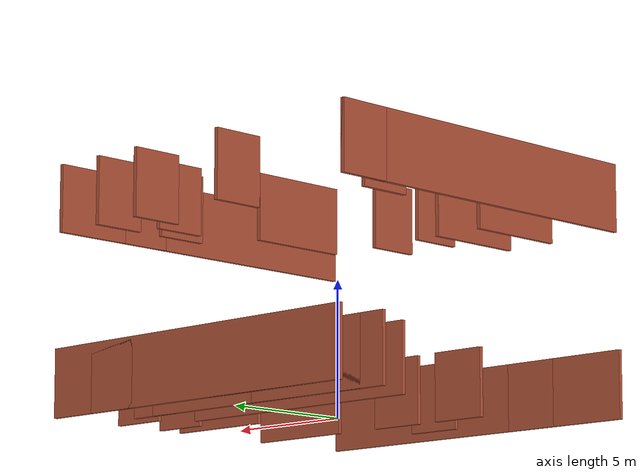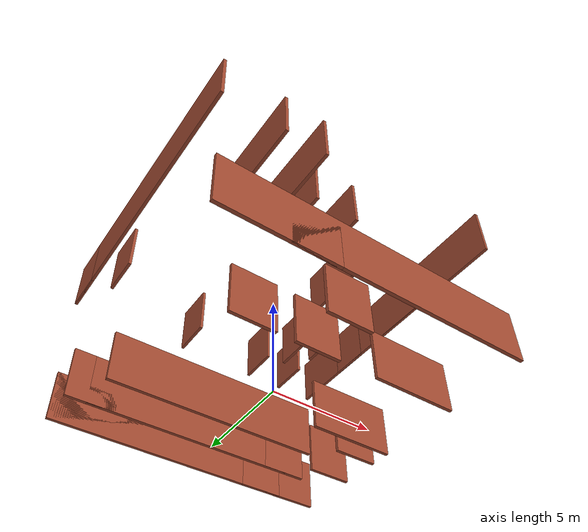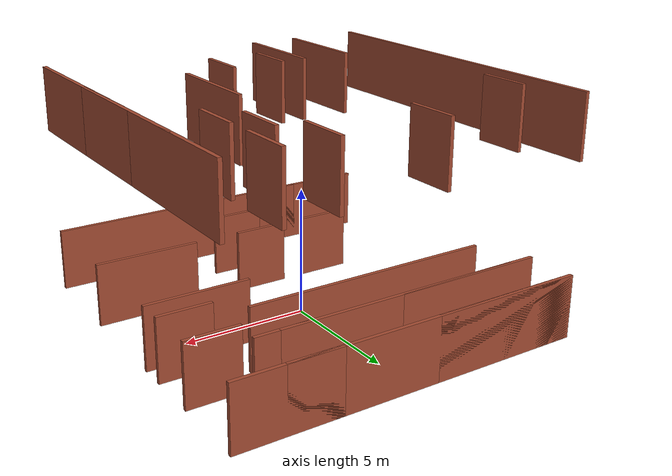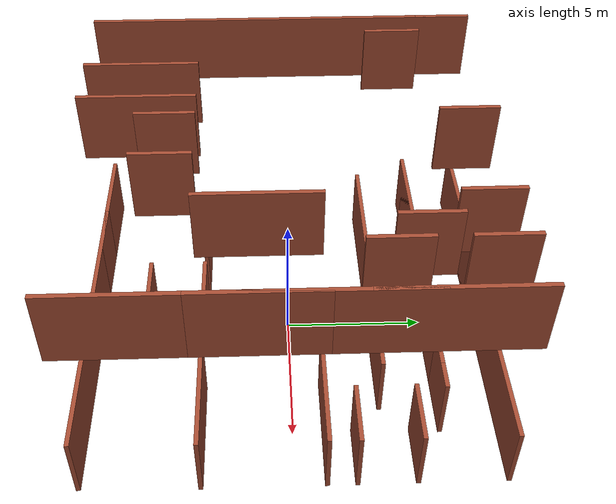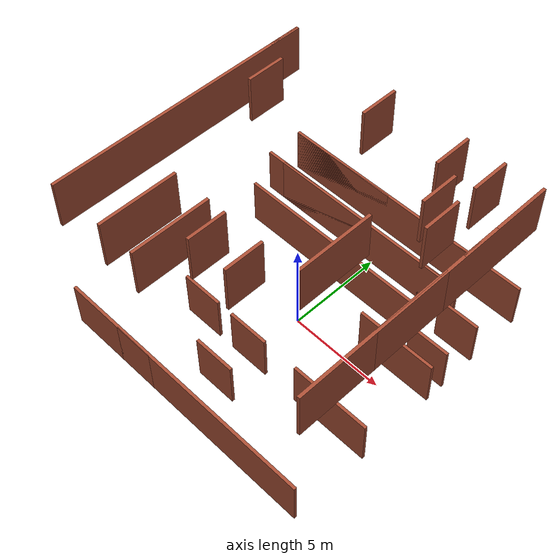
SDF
<?xml version='1.0'?>
<sdf version='1.6'>
  <model name='random_world'>
    <link name='Wall_101'>
      <pose frame=''>-7.075 0 0 0 0 -1.5708</pose>
      <self_collide>0</self_collide>
      <kinematic>0</kinematic>
      <visual name='Wall_101_Visual'>
        <pose frame=''>0 0 8 0 -0 0</pose>
        <geometry>
          <box>
            <size>14 0.15 2.5</size>
          </box>
        </geometry>
        <material>
          <script>
            <uri>file://media/materials/scripts/gazebo.material</uri>
            <name>Gazebo/Bricks</name>
          </script>
          <ambient>1 1 1 1</ambient>
          <diffuse>1 1 1 1</diffuse>
          <specular>0.2 0.2 0.2 1</specular>
          <emissive>0 0 0 1</emissive>
        </material>
        <cast_shadows>1</cast_shadows>
        <transparency>0</transparency>
      </visual>
      <collision name='Wall_101_Collision'>
        <laser_retro>0</laser_retro>
        <max_contacts>10</max_contacts>
        <pose frame=''>0 0 8 0 -0 0</pose>
        <geometry>
          <box>
            <size>14 0.15 2.5</size>
          </box>
        </geometry>
        <surface>
          <friction>
            <ode>
              <mu>1</mu>
              <mu2>1</mu2>
              <fdir1>0 0 0</fdir1>
              <slip1>0</slip1>
              <slip2>0</slip2>
            </ode>
            <torsional>
              <coefficient>1</coefficient>
              <patch_radius>0</patch_radius>
              <surface_radius>0</surface_radius>
              <use_patch_radius>1</use_patch_radius>
              <ode>
                <slip>0</slip>
              </ode>
            </torsional>
          </friction>
          <bounce>
            <restitution_coefficient>0</restitution_coefficient>
            <threshold>1e+06</threshold>
          </bounce>
          <contact>
            <collide_without_contact>0</collide_without_contact>
            <collide_without_contact_bitmask>1</collide_without_contact_bitmask>
            <collide_bitmask>1</collide_bitmask>
            <ode>
              <soft_cfm>0</soft_cfm>
              <soft_erp>0.2</soft_erp>
              <kp>1e+13</kp>
              <kd>1</kd>
              <max_vel>0.01</max_vel>
              <min_depth>0</min_depth>
            </ode>
            <bullet>
              <split_impulse>1</split_impulse>
              <split_impulse_penetration_threshold>-0.01</split_impulse_penetration_threshold>
              <soft_cfm>0</soft_cfm>
              <soft_erp>0.2</soft_erp>
              <kp>1e+13</kp>
              <kd>1</kd>
            </bullet>
          </contact>
        </surface>
      </collision>
    </link>
    <link name='Wall_102'>
      <pose frame=''>-4 7.075 0 0 -0 0</pose>
      <self_collide>0</self_collide>
      <kinematic>0</kinematic>
      <visual name='Wall_102_Visual'>
        <pose frame=''>4 0 1.25 0 -0 0</pose>
        <geometry>
          <box>
            <size>14.15 0.15 2.5</size>
          </box>
        </geometry>
        <material>
          <script>
            <uri>file://media/materials/scripts/gazebo.material</uri>
            <name>Gazebo/Bricks</name>
          </script>
          <ambient>1 1 1 1</ambient>
          <diffuse>1 1 1 1</diffuse>
          <specular>0.2 0.2 0.2 1</specular>
          <emissive>0 0 0 1</emissive>
        </material>
        <cast_shadows>1</cast_shadows>
        <transparency>0</transparency>
      </visual>
      <collision name='Wall_102_Collision'>
        <laser_retro>0</laser_retro>
        <max_contacts>10</max_contacts>
        <pose frame=''>4 0 1.25 0 -0 0</pose>
        <geometry>
          <box>
            <size>14.15 0.15 2.5</size>
          </box>
        </geometry>
        <surface>
          <friction>
            <ode>
              <mu>1</mu>
              <mu2>1</mu2>
              <fdir1>0 0 0</fdir1>
              <slip1>0</slip1>
              <slip2>0</slip2>
            </ode>
            <torsional>
              <coefficient>1</coefficient>
              <patch_radius>0</patch_radius>
              <surface_radius>0</surface_radius>
              <use_patch_radius>1</use_patch_radius>
              <ode>
                <slip>0</slip>
              </ode>
            </torsional>
          </friction>
          <bounce>
            <restitution_coefficient>0</restitution_coefficient>
            <threshold>1e+06</threshold>
          </bounce>
          <contact>
            <collide_without_contact>0</collide_without_contact>
            <collide_without_contact_bitmask>1</collide_without_contact_bitmask>
            <collide_bitmask>1</collide_bitmask>
            <ode>
              <soft_cfm>0</soft_cfm>
              <soft_erp>0.2</soft_erp>
              <kp>1e+13</kp>
              <kd>1</kd>
              <max_vel>0.01</max_vel>
              <min_depth>0</min_depth>
            </ode>
            <bullet>
              <split_impulse>1</split_impulse>
              <split_impulse_penetration_threshold>-0.01</split_impulse_penetration_threshold>
              <soft_cfm>0</soft_cfm>
              <soft_erp>0.2</soft_erp>
              <kp>1e+13</kp>
              <kd>1</kd>
            </bullet>
          </contact>
        </surface>
      </collision>
    </link>
    <link name='Wall_103'>
      <pose frame=''>7.075 0 0 0 0 -1.5708</pose>
      <self_collide>0</self_collide>
      <kinematic>0</kinematic>
      <visual name='Wall_103_Visual'>
        <pose frame=''>0 0 8 0 -0 0</pose>
        <geometry>
          <box>
            <size>14 0.15 2.5</size>
          </box>
        </geometry>
        <material>
          <script>
            <uri>file://media/materials/scripts/gazebo.material</uri>
            <name>Gazebo/Bricks</name>
          </script>
          <ambient>1 1 1 1</ambient>
          <diffuse>1 1 1 1</diffuse>
          <specular>0.2 0.2 0.2 1</specular>
          <emissive>0 0 0 1</emissive>
        </material>
        <cast_shadows>1</cast_shadows>
        <transparency>0</transparency>
      </visual>
      <collision name='Wall_103_Collision'>
        <laser_retro>0</laser_retro>
        <max_contacts>10</max_contacts>
        <pose frame=''>0 0 8 0 -0 0</pose>
        <geometry>
          <box>
            <size>14 0.15 2.5</size>
          </box>
        </geometry>
        <surface>
          <friction>
            <ode>
              <mu>1</mu>
              <mu2>1</mu2>
              <fdir1>0 0 0</fdir1>
              <slip1>0</slip1>
              <slip2>0</slip2>
            </ode>
            <torsional>
              <coefficient>1</coefficient>
              <patch_radius>0</patch_radius>
              <surface_radius>0</surface_radius>
              <use_patch_radius>1</use_patch_radius>
              <ode>
                <slip>0</slip>
              </ode>
            </torsional>
          </friction>
          <bounce>
            <restitution_coefficient>0</restitution_coefficient>
            <threshold>1e+06</threshold>
          </bounce>
          <contact>
            <collide_without_contact>0</collide_without_contact>
            <collide_without_contact_bitmask>1</collide_without_contact_bitmask>
            <collide_bitmask>1</collide_bitmask>
            <ode>
              <soft_cfm>0</soft_cfm>
              <soft_erp>0.2</soft_erp>
              <kp>1e+13</kp>
              <kd>1</kd>
              <max_vel>0.01</max_vel>
              <min_depth>0</min_depth>
            </ode>
            <bullet>
              <split_impulse>1</split_impulse>
              <split_impulse_penetration_threshold>-0.01</split_impulse_penetration_threshold>
              <soft_cfm>0</soft_cfm>
              <soft_erp>0.2</soft_erp>
              <kp>1e+13</kp>
              <kd>1</kd>
            </bullet>
          </contact>
        </surface>
      </collision>
    </link>
    <link name='Wall_104'>
      <pose frame=''>-4 -7.075 0 0 -0 0</pose>
      <self_collide>0</self_collide>
      <kinematic>0</kinematic>
      <visual name='Wall_104_Visual'>
        <pose frame=''>3.925 0 1.25 0 -0 0</pose>
        <geometry>
          <box>
            <size>14.15 0.15 2.5</size>
          </box>
        </geometry>
        <material>
          <script>
            <uri>file://media/materials/scripts/gazebo.material</uri>
            <name>Gazebo/Bricks</name>
          </script>
          <ambient>1 1 1 1</ambient>
          <diffuse>1 1 1 1</diffuse>
          <specular>0.2 0.2 0.2 1</specular>
          <emissive>0 0 0 1</emissive>
        </material>
        <cast_shadows>1</cast_shadows>
        <transparency>0</transparency>
      </visual>
      <collision name='Wall_104_Collision'>
        <laser_retro>0</laser_retro>
        <max_contacts>10</max_contacts>
        <pose frame=''>3.925 0 1.25 0 -0 0</pose>
        <geometry>
          <box>
            <size>14.15 0.15 2.5</size>
          </box>
        </geometry>
        <surface>
          <friction>
            <ode>
              <mu>1</mu>
              <mu2>1</mu2>
              <fdir1>0 0 0</fdir1>
              <slip1>0</slip1>
              <slip2>0</slip2>
            </ode>
            <torsional>
              <coefficient>1</coefficient>
              <patch_radius>0</patch_radius>
              <surface_radius>0</surface_radius>
              <use_patch_radius>1</use_patch_radius>
              <ode>
                <slip>0</slip>
              </ode>
            </torsional>
          </friction>
          <bounce>
            <restitution_coefficient>0</restitution_coefficient>
            <threshold>1e+06</threshold>
          </bounce>
          <contact>
            <collide_without_contact>0</collide_without_contact>
            <collide_without_contact_bitmask>1</collide_without_contact_bitmask>
            <collide_bitmask>1</collide_bitmask>
            <ode>
              <soft_cfm>0</soft_cfm>
              <soft_erp>0.2</soft_erp>
              <kp>1e+13</kp>
              <kd>1</kd>
              <max_vel>0.01</max_vel>
              <min_depth>0</min_depth>
            </ode>
            <bullet>
              <split_impulse>1</split_impulse>
              <split_impulse_penetration_threshold>-0.01</split_impulse_penetration_threshold>
              <soft_cfm>0</soft_cfm>
              <soft_erp>0.2</soft_erp>
              <kp>1e+13</kp>
              <kd>1</kd>
            </bullet>
          </contact>
        </surface>
      </collision>
    </link>
    <link name='Wall_Room_H_1'>
      <pose frame=''>7.075 -1 0 0 0 -1.5708</pose>
      <self_collide>0</self_collide>
      <kinematic>0</kinematic>
      <visual name='Wall_Room_H_1_Visual'>
        <pose frame=''>0 0 8 0 -0 0</pose>
        <geometry>
          <box>
            <size>4 0.15 2.5</size>
          </box>
        </geometry>
        <material>
          <script>
            <uri>file://media/materials/scripts/gazebo.material</uri>
            <name>Gazebo/Bricks</name>
          </script>
          <ambient>1 1 1 1</ambient>
          <diffuse>1 1 1 1</diffuse>
          <specular>0.2 0.2 0.2 1</specular>
          <emissive>0 0 0 1</emissive>
        </material>
        <cast_shadows>1</cast_shadows>
        <transparency>0</transparency>
      </visual>
      <collision name='Wall_Room_H_1_Collision'>
        <laser_retro>0</laser_retro>
        <max_contacts>10</max_contacts>
        <pose frame=''>0 0 8 0 -0 0</pose>
        <geometry>
          <box>
            <size>4 0.15 2.5</size>
          </box>
        </geometry>
        <surface>
          <friction>
            <ode>
              <mu>1</mu>
              <mu2>1</mu2>
              <fdir1>0 0 0</fdir1>
              <slip1>0</slip1>
              <slip2>0</slip2>
            </ode>
            <torsional>
              <coefficient>1</coefficient>
              <patch_radius>0</patch_radius>
              <surface_radius>0</surface_radius>
              <use_patch_radius>1</use_patch_radius>
              <ode>
                <slip>0</slip>
              </ode>
            </torsional>
          </friction>
          <bounce>
            <restitution_coefficient>0</restitution_coefficient>
            <threshold>1e+06</threshold>
          </bounce>
          <contact>
            <collide_without_contact>0</collide_without_contact>
            <collide_without_contact_bitmask>1</collide_without_contact_bitmask>
            <collide_bitmask>1</collide_bitmask>
            <ode>
              <soft_cfm>0</soft_cfm>
              <soft_erp>0.2</soft_erp>
              <kp>1e+13</kp>
              <kd>1</kd>
              <max_vel>0.01</max_vel>
              <min_depth>0</min_depth>
            </ode>
            <bullet>
              <split_impulse>1</split_impulse>
              <split_impulse_penetration_threshold>-0.01</split_impulse_penetration_threshold>
              <soft_cfm>0</soft_cfm>
              <soft_erp>0.2</soft_erp>
              <kp>1e+13</kp>
              <kd>1</kd>
            </bullet>
          </contact>
        </surface>
      </collision>
    </link>
    <link name='Wall_Room_H_2'>
      <pose frame=''>3.075 -1 0 0 0 -1.5708</pose>
      <self_collide>0</self_collide>
      <kinematic>0</kinematic>
      <visual name='Wall_Room_H_2_Visual'>
        <pose frame=''>0 0 8 0 -0 0</pose>
        <geometry>
          <box>
            <size>4 0.15 2.5</size>
          </box>
        </geometry>
        <material>
          <script>
            <uri>file://media/materials/scripts/gazebo.material</uri>
            <name>Gazebo/Bricks</name>
          </script>
          <ambient>1 1 1 1</ambient>
          <diffuse>1 1 1 1</diffuse>
          <specular>0.2 0.2 0.2 1</specular>
          <emissive>0 0 0 1</emissive>
        </material>
        <cast_shadows>1</cast_shadows>
        <transparency>0</transparency>
      </visual>
      <collision name='Wall_Room_H_2_Collision'>
        <laser_retro>0</laser_retro>
        <max_contacts>10</max_contacts>
        <pose frame=''>0 0 8 0 -0 0</pose>
        <geometry>
          <box>
            <size>4 0.15 2.5</size>
          </box>
        </geometry>
        <surface>
          <friction>
            <ode>
              <mu>1</mu>
              <mu2>1</mu2>
              <fdir1>0 0 0</fdir1>
              <slip1>0</slip1>
              <slip2>0</slip2>
            </ode>
            <torsional>
              <coefficient>1</coefficient>
              <patch_radius>0</patch_radius>
              <surface_radius>0</surface_radius>
              <use_patch_radius>1</use_patch_radius>
              <ode>
                <slip>0</slip>
              </ode>
            </torsional>
          </friction>
          <bounce>
            <restitution_coefficient>0</restitution_coefficient>
            <threshold>1e+06</threshold>
          </bounce>
          <contact>
            <collide_without_contact>0</collide_without_contact>
            <collide_without_contact_bitmask>1</collide_without_contact_bitmask>
            <collide_bitmask>1</collide_bitmask>
            <ode>
              <soft_cfm>0</soft_cfm>
              <soft_erp>0.2</soft_erp>
              <kp>1e+13</kp>
              <kd>1</kd>
              <max_vel>0.01</max_vel>
              <min_depth>0</min_depth>
            </ode>
            <bullet>
              <split_impulse>1</split_impulse>
              <split_impulse_penetration_threshold>-0.01</split_impulse_penetration_threshold>
              <soft_cfm>0</soft_cfm>
              <soft_erp>0.2</soft_erp>
              <kp>1e+13</kp>
              <kd>1</kd>
            </bullet>
          </contact>
        </surface>
      </collision>
    </link>
    <link name='Wall_Room_V_3'>
      <pose frame=''>5 1.075 0 0 -0 0</pose>
      <self_collide>0</self_collide>
      <kinematic>0</kinematic>
      <visual name='Wall_Room_V_3_Visual'>
        <pose frame=''>0 0 1.25 0 -0 0</pose>
        <geometry>
          <box>
            <size>4.15 0.15 2.5</size>
          </box>
        </geometry>
        <material>
          <script>
            <uri>file://media/materials/scripts/gazebo.material</uri>
            <name>Gazebo/Bricks</name>
          </script>
          <ambient>1 1 1 1</ambient>
          <diffuse>1 1 1 1</diffuse>
          <specular>0.2 0.2 0.2 1</specular>
          <emissive>0 0 0 1</emissive>
        </material>
        <cast_shadows>1</cast_shadows>
        <transparency>0</transparency>
      </visual>
      <collision name='Wall_Room_V_3_Collision'>
        <laser_retro>0</laser_retro>
        <max_contacts>10</max_contacts>
        <pose frame=''>0 0 1.25 0 -0 0</pose>
        <geometry>
          <box>
            <size>4.15 0.15 2.5</size>
          </box>
        </geometry>
        <surface>
          <friction>
            <ode>
              <mu>1</mu>
              <mu2>1</mu2>
              <fdir1>0 0 0</fdir1>
              <slip1>0</slip1>
              <slip2>0</slip2>
            </ode>
            <torsional>
              <coefficient>1</coefficient>
              <patch_radius>0</patch_radius>
              <surface_radius>0</surface_radius>
              <use_patch_radius>1</use_patch_radius>
              <ode>
                <slip>0</slip>
              </ode>
            </torsional>
          </friction>
          <bounce>
            <restitution_coefficient>0</restitution_coefficient>
            <threshold>1e+06</threshold>
          </bounce>
          <contact>
            <collide_without_contact>0</collide_without_contact>
            <collide_without_contact_bitmask>1</collide_without_contact_bitmask>
            <collide_bitmask>1</collide_bitmask>
            <ode>
              <soft_cfm>0</soft_cfm>
              <soft_erp>0.2</soft_erp>
              <kp>1e+13</kp>
              <kd>1</kd>
              <max_vel>0.01</max_vel>
              <min_depth>0</min_depth>
            </ode>
            <bullet>
              <split_impulse>1</split_impulse>
              <split_impulse_penetration_threshold>-0.01</split_impulse_penetration_threshold>
              <soft_cfm>0</soft_cfm>
              <soft_erp>0.2</soft_erp>
              <kp>1e+13</kp>
              <kd>1</kd>
            </bullet>
          </contact>
        </surface>
      </collision>
    </link>
    <link name='Wall_Room_V_4'>
      <pose frame=''>5 -3.075 0 0 -0 0</pose>
      <self_collide>0</self_collide>
      <kinematic>0</kinematic>
      <visual name='Wall_Room_V_4_Visual'>
        <pose frame=''>0 0 1.25 0 -0 0</pose>
        <geometry>
          <box>
            <size>4.15 0.15 2.5</size>
          </box>
        </geometry>
        <material>
          <script>
            <uri>file://media/materials/scripts/gazebo.material</uri>
            <name>Gazebo/Bricks</name>
          </script>
          <ambient>1 1 1 1</ambient>
          <diffuse>1 1 1 1</diffuse>
          <specular>0.2 0.2 0.2 1</specular>
          <emissive>0 0 0 1</emissive>
        </material>
        <cast_shadows>1</cast_shadows>
        <transparency>0</transparency>
      </visual>
      <collision name='Wall_Room_V_4_Collision'>
        <laser_retro>0</laser_retro>
        <max_contacts>10</max_contacts>
        <pose frame=''>0 0 1.25 0 -0 0</pose>
        <geometry>
          <box>
            <size>4.15 0.15 2.5</size>
          </box>
        </geometry>
        <surface>
          <friction>
            <ode>
              <mu>1</mu>
              <mu2>1</mu2>
              <fdir1>0 0 0</fdir1>
              <slip1>0</slip1>
              <slip2>0</slip2>
            </ode>
            <torsional>
              <coefficient>1</coefficient>
              <patch_radius>0</patch_radius>
              <surface_radius>0</surface_radius>
              <use_patch_radius>1</use_patch_radius>
              <ode>
                <slip>0</slip>
              </ode>
            </torsional>
          </friction>
          <bounce>
            <restitution_coefficient>0</restitution_coefficient>
            <threshold>1e+06</threshold>
          </bounce>
          <contact>
            <collide_without_contact>0</collide_without_contact>
            <collide_without_contact_bitmask>1</collide_without_contact_bitmask>
            <collide_bitmask>1</collide_bitmask>
            <ode>
              <soft_cfm>0</soft_cfm>
              <soft_erp>0.2</soft_erp>
              <kp>1e+13</kp>
              <kd>1</kd>
              <max_vel>0.01</max_vel>
              <min_depth>0</min_depth>
            </ode>
            <bullet>
              <split_impulse>1</split_impulse>
              <split_impulse_penetration_threshold>-0.01</split_impulse_penetration_threshold>
              <soft_cfm>0</soft_cfm>
              <soft_erp>0.2</soft_erp>
              <kp>1e+13</kp>
              <kd>1</kd>
            </bullet>
          </contact>
        </surface>
      </collision>
    </link>
    <link name='Wall_Room_H_5'>
      <pose frame=''>4.075 4 0 0 0 -1.5708</pose>
      <self_collide>0</self_collide>
      <kinematic>0</kinematic>
      <visual name='Wall_Room_H_5_Visual'>
        <pose frame=''>0 0 8 0 -0 0</pose>
        <geometry>
          <box>
            <size>2 0.15 2.5</size>
          </box>
        </geometry>
        <material>
          <script>
            <uri>file://media/materials/scripts/gazebo.material</uri>
            <name>Gazebo/Bricks</name>
          </script>
          <ambient>1 1 1 1</ambient>
          <diffuse>1 1 1 1</diffuse>
          <specular>0.2 0.2 0.2 1</specular>
          <emissive>0 0 0 1</emissive>
        </material>
        <cast_shadows>1</cast_shadows>
        <transparency>0</transparency>
      </visual>
      <collision name='Wall_Room_H_5_Collision'>
        <laser_retro>0</laser_retro>
        <max_contacts>10</max_contacts>
        <pose frame=''>0 0 8 0 -0 0</pose>
        <geometry>
          <box>
            <size>2 0.15 2.5</size>
          </box>
        </geometry>
        <surface>
          <friction>
            <ode>
              <mu>1</mu>
              <mu2>1</mu2>
              <fdir1>0 0 0</fdir1>
              <slip1>0</slip1>
              <slip2>0</slip2>
            </ode>
            <torsional>
              <coefficient>1</coefficient>
              <patch_radius>0</patch_radius>
              <surface_radius>0</surface_radius>
              <use_patch_radius>1</use_patch_radius>
              <ode>
                <slip>0</slip>
              </ode>
            </torsional>
          </friction>
          <bounce>
            <restitution_coefficient>0</restitution_coefficient>
            <threshold>1e+06</threshold>
          </bounce>
          <contact>
            <collide_without_contact>0</collide_without_contact>
            <collide_without_contact_bitmask>1</collide_without_contact_bitmask>
            <collide_bitmask>1</collide_bitmask>
            <ode>
              <soft_cfm>0</soft_cfm>
              <soft_erp>0.2</soft_erp>
              <kp>1e+13</kp>
              <kd>1</kd>
              <max_vel>0.01</max_vel>
              <min_depth>0</min_depth>
            </ode>
            <bullet>
              <split_impulse>1</split_impulse>
              <split_impulse_penetration_threshold>-0.01</split_impulse_penetration_threshold>
              <soft_cfm>0</soft_cfm>
              <soft_erp>0.2</soft_erp>
              <kp>1e+13</kp>
              <kd>1</kd>
            </bullet>
          </contact>
        </surface>
      </collision>
    </link>
    <link name='Wall_Room_H_6'>
      <pose frame=''>-6.075 4 0 0 0 -1.5708</pose>
      <self_collide>0</self_collide>
      <kinematic>0</kinematic>
      <visual name='Wall_Room_H_6_Visual'>
        <pose frame=''>0 0 8 0 -0 0</pose>
        <geometry>
          <box>
            <size>2 0.15 2.5</size>
          </box>
        </geometry>
        <material>
          <script>
            <uri>file://media/materials/scripts/gazebo.material</uri>
            <name>Gazebo/Bricks</name>
          </script>
          <ambient>1 1 1 1</ambient>
          <diffuse>1 1 1 1</diffuse>
          <specular>0.2 0.2 0.2 1</specular>
          <emissive>0 0 0 1</emissive>
        </material>
        <cast_shadows>1</cast_shadows>
        <transparency>0</transparency>
      </visual>
      <collision name='Wall_Room_H_6_Collision'>
        <laser_retro>0</laser_retro>
        <max_contacts>10</max_contacts>
        <pose frame=''>0 0 8 0 -0 0</pose>
        <geometry>
          <box>
            <size>2 0.15 2.5</size>
          </box>
        </geometry>
        <surface>
          <friction>
            <ode>
              <mu>1</mu>
              <mu2>1</mu2>
              <fdir1>0 0 0</fdir1>
              <slip1>0</slip1>
              <slip2>0</slip2>
            </ode>
            <torsional>
              <coefficient>1</coefficient>
              <patch_radius>0</patch_radius>
              <surface_radius>0</surface_radius>
              <use_patch_radius>1</use_patch_radius>
              <ode>
                <slip>0</slip>
              </ode>
            </torsional>
          </friction>
          <bounce>
            <restitution_coefficient>0</restitution_coefficient>
            <threshold>1e+06</threshold>
          </bounce>
          <contact>
            <collide_without_contact>0</collide_without_contact>
            <collide_without_contact_bitmask>1</collide_without_contact_bitmask>
            <collide_bitmask>1</collide_bitmask>
            <ode>
              <soft_cfm>0</soft_cfm>
              <soft_erp>0.2</soft_erp>
              <kp>1e+13</kp>
              <kd>1</kd>
              <max_vel>0.01</max_vel>
              <min_depth>0</min_depth>
            </ode>
            <bullet>
              <split_impulse>1</split_impulse>
              <split_impulse_penetration_threshold>-0.01</split_impulse_penetration_threshold>
              <soft_cfm>0</soft_cfm>
              <soft_erp>0.2</soft_erp>
              <kp>1e+13</kp>
              <kd>1</kd>
            </bullet>
          </contact>
        </surface>
      </collision>
    </link>
    <link name='Wall_Room_V_7'>
      <pose frame=''>-1 5.075 0 0 -0 0</pose>
      <self_collide>0</self_collide>
      <kinematic>0</kinematic>
      <visual name='Wall_Room_V_7_Visual'>
        <pose frame=''>0 0 1.25 0 -0 0</pose>
        <geometry>
          <box>
            <size>10.15 0.15 2.5</size>
          </box>
        </geometry>
        <material>
          <script>
            <uri>file://media/materials/scripts/gazebo.material</uri>
            <name>Gazebo/Bricks</name>
          </script>
          <ambient>1 1 1 1</ambient>
          <diffuse>1 1 1 1</diffuse>
          <specular>0.2 0.2 0.2 1</specular>
          <emissive>0 0 0 1</emissive>
        </material>
        <cast_shadows>1</cast_shadows>
        <transparency>0</transparency>
      </visual>
      <collision name='Wall_Room_V_7_Collision'>
        <laser_retro>0</laser_retro>
        <max_contacts>10</max_contacts>
        <pose frame=''>0 0 1.25 0 -0 0</pose>
        <geometry>
          <box>
            <size>10.15 0.15 2.5</size>
          </box>
        </geometry>
        <surface>
          <friction>
            <ode>
              <mu>1</mu>
              <mu2>1</mu2>
              <fdir1>0 0 0</fdir1>
              <slip1>0</slip1>
              <slip2>0</slip2>
            </ode>
            <torsional>
              <coefficient>1</coefficient>
              <patch_radius>0</patch_radius>
              <surface_radius>0</surface_radius>
              <use_patch_radius>1</use_patch_radius>
              <ode>
                <slip>0</slip>
              </ode>
            </torsional>
          </friction>
          <bounce>
            <restitution_coefficient>0</restitution_coefficient>
            <threshold>1e+06</threshold>
          </bounce>
          <contact>
            <collide_without_contact>0</collide_without_contact>
            <collide_without_contact_bitmask>1</collide_without_contact_bitmask>
            <collide_bitmask>1</collide_bitmask>
            <ode>
              <soft_cfm>0</soft_cfm>
              <soft_erp>0.2</soft_erp>
              <kp>1e+13</kp>
              <kd>1</kd>
              <max_vel>0.01</max_vel>
              <min_depth>0</min_depth>
            </ode>
            <bullet>
              <split_impulse>1</split_impulse>
              <split_impulse_penetration_threshold>-0.01</split_impulse_penetration_threshold>
              <soft_cfm>0</soft_cfm>
              <soft_erp>0.2</soft_erp>
              <kp>1e+13</kp>
              <kd>1</kd>
            </bullet>
          </contact>
        </surface>
      </collision>
    </link>
    <link name='Wall_Room_V_8'>
      <pose frame=''>-1 3.075 0 0 -0 0</pose>
      <self_collide>0</self_collide>
      <kinematic>0</kinematic>
      <visual name='Wall_Room_V_8_Visual'>
        <pose frame=''>0 0 1.25 0 -0 0</pose>
        <geometry>
          <box>
            <size>10.15 0.15 2.5</size>
          </box>
        </geometry>
        <material>
          <script>
            <uri>file://media/materials/scripts/gazebo.material</uri>
            <name>Gazebo/Bricks</name>
          </script>
          <ambient>1 1 1 1</ambient>
          <diffuse>1 1 1 1</diffuse>
          <specular>0.2 0.2 0.2 1</specular>
          <emissive>0 0 0 1</emissive>
        </material>
        <cast_shadows>1</cast_shadows>
        <transparency>0</transparency>
      </visual>
      <collision name='Wall_Room_V_8_Collision'>
        <laser_retro>0</laser_retro>
        <max_contacts>10</max_contacts>
        <pose frame=''>0 0 1.25 0 -0 0</pose>
        <geometry>
          <box>
            <size>10.15 0.15 2.5</size>
          </box>
        </geometry>
        <surface>
          <friction>
            <ode>
              <mu>1</mu>
              <mu2>1</mu2>
              <fdir1>0 0 0</fdir1>
              <slip1>0</slip1>
              <slip2>0</slip2>
            </ode>
            <torsional>
              <coefficient>1</coefficient>
              <patch_radius>0</patch_radius>
              <surface_radius>0</surface_radius>
              <use_patch_radius>1</use_patch_radius>
              <ode>
                <slip>0</slip>
              </ode>
            </torsional>
          </friction>
          <bounce>
            <restitution_coefficient>0</restitution_coefficient>
            <threshold>1e+06</threshold>
          </bounce>
          <contact>
            <collide_without_contact>0</collide_without_contact>
            <collide_without_contact_bitmask>1</collide_without_contact_bitmask>
            <collide_bitmask>1</collide_bitmask>
            <ode>
              <soft_cfm>0</soft_cfm>
              <soft_erp>0.2</soft_erp>
              <kp>1e+13</kp>
              <kd>1</kd>
              <max_vel>0.01</max_vel>
              <min_depth>0</min_depth>
            </ode>
            <bullet>
              <split_impulse>1</split_impulse>
              <split_impulse_penetration_threshold>-0.01</split_impulse_penetration_threshold>
              <soft_cfm>0</soft_cfm>
              <soft_erp>0.2</soft_erp>
              <kp>1e+13</kp>
              <kd>1</kd>
            </bullet>
          </contact>
        </surface>
      </collision>
    </link>
    <link name='Wall_Room_H_9'>
      <pose frame=''>5.075 6 0 0 0 -1.5708</pose>
      <self_collide>0</self_collide>
      <kinematic>0</kinematic>
      <visual name='Wall_Room_H_9_Visual'>
        <pose frame=''>0 0 8 0 -0 0</pose>
        <geometry>
          <box>
            <size>2 0.15 2.5</size>
          </box>
        </geometry>
        <material>
          <script>
            <uri>file://media/materials/scripts/gazebo.material</uri>
            <name>Gazebo/Bricks</name>
          </script>
          <ambient>1 1 1 1</ambient>
          <diffuse>1 1 1 1</diffuse>
          <specular>0.2 0.2 0.2 1</specular>
          <emissive>0 0 0 1</emissive>
        </material>
        <cast_shadows>1</cast_shadows>
        <transparency>0</transparency>
      </visual>
      <collision name='Wall_Room_H_9_Collision'>
        <laser_retro>0</laser_retro>
        <max_contacts>10</max_contacts>
        <pose frame=''>0 0 8 0 -0 0</pose>
        <geometry>
          <box>
            <size>2 0.15 2.5</size>
          </box>
        </geometry>
        <surface>
          <friction>
            <ode>
              <mu>1</mu>
              <mu2>1</mu2>
              <fdir1>0 0 0</fdir1>
              <slip1>0</slip1>
              <slip2>0</slip2>
            </ode>
            <torsional>
              <coefficient>1</coefficient>
              <patch_radius>0</patch_radius>
              <surface_radius>0</surface_radius>
              <use_patch_radius>1</use_patch_radius>
              <ode>
                <slip>0</slip>
              </ode>
            </torsional>
          </friction>
          <bounce>
            <restitution_coefficient>0</restitution_coefficient>
            <threshold>1e+06</threshold>
          </bounce>
          <contact>
            <collide_without_contact>0</collide_without_contact>
            <collide_without_contact_bitmask>1</collide_without_contact_bitmask>
            <collide_bitmask>1</collide_bitmask>
            <ode>
              <soft_cfm>0</soft_cfm>
              <soft_erp>0.2</soft_erp>
              <kp>1e+13</kp>
              <kd>1</kd>
              <max_vel>0.01</max_vel>
              <min_depth>0</min_depth>
            </ode>
            <bullet>
              <split_impulse>1</split_impulse>
              <split_impulse_penetration_threshold>-0.01</split_impulse_penetration_threshold>
              <soft_cfm>0</soft_cfm>
              <soft_erp>0.2</soft_erp>
              <kp>1e+13</kp>
              <kd>1</kd>
            </bullet>
          </contact>
        </surface>
      </collision>
    </link>
    <link name='Wall_Room_H_10'>
      <pose frame=''>3.075 6 0 0 0 -1.5708</pose>
      <self_collide>0</self_collide>
      <kinematic>0</kinematic>
      <visual name='Wall_Room_H_10_Visual'>
        <pose frame=''>0 0 8 0 -0 0</pose>
        <geometry>
          <box>
            <size>2 0.15 2.5</size>
          </box>
        </geometry>
        <material>
          <script>
            <uri>file://media/materials/scripts/gazebo.material</uri>
            <name>Gazebo/Bricks</name>
          </script>
          <ambient>1 1 1 1</ambient>
          <diffuse>1 1 1 1</diffuse>
          <specular>0.2 0.2 0.2 1</specular>
          <emissive>0 0 0 1</emissive>
        </material>
        <cast_shadows>1</cast_shadows>
        <transparency>0</transparency>
      </visual>
      <collision name='Wall_Room_H_10_Collision'>
        <laser_retro>0</laser_retro>
        <max_contacts>10</max_contacts>
        <pose frame=''>0 0 8 0 -0 0</pose>
        <geometry>
          <box>
            <size>2 0.15 2.5</size>
          </box>
        </geometry>
        <surface>
          <friction>
            <ode>
              <mu>1</mu>
              <mu2>1</mu2>
              <fdir1>0 0 0</fdir1>
              <slip1>0</slip1>
              <slip2>0</slip2>
            </ode>
            <torsional>
              <coefficient>1</coefficient>
              <patch_radius>0</patch_radius>
              <surface_radius>0</surface_radius>
              <use_patch_radius>1</use_patch_radius>
              <ode>
                <slip>0</slip>
              </ode>
            </torsional>
          </friction>
          <bounce>
            <restitution_coefficient>0</restitution_coefficient>
            <threshold>1e+06</threshold>
          </bounce>
          <contact>
            <collide_without_contact>0</collide_without_contact>
            <collide_without_contact_bitmask>1</collide_without_contact_bitmask>
            <collide_bitmask>1</collide_bitmask>
            <ode>
              <soft_cfm>0</soft_cfm>
              <soft_erp>0.2</soft_erp>
              <kp>1e+13</kp>
              <kd>1</kd>
              <max_vel>0.01</max_vel>
              <min_depth>0</min_depth>
            </ode>
            <bullet>
              <split_impulse>1</split_impulse>
              <split_impulse_penetration_threshold>-0.01</split_impulse_penetration_threshold>
              <soft_cfm>0</soft_cfm>
              <soft_erp>0.2</soft_erp>
              <kp>1e+13</kp>
              <kd>1</kd>
            </bullet>
          </contact>
        </surface>
      </collision>
    </link>
    <link name='Wall_Room_V_11'>
      <pose frame=''>4 7.075 0 0 -0 0</pose>
      <self_collide>0</self_collide>
      <kinematic>0</kinematic>
      <visual name='Wall_Room_V_11_Visual'>
        <pose frame=''>0 0 1.25 0 -0 0</pose>
        <geometry>
          <box>
            <size>2.15 0.15 2.5</size>
          </box>
        </geometry>
        <material>
          <script>
            <uri>file://media/materials/scripts/gazebo.material</uri>
            <name>Gazebo/Bricks</name>
          </script>
          <ambient>1 1 1 1</ambient>
          <diffuse>1 1 1 1</diffuse>
          <specular>0.2 0.2 0.2 1</specular>
          <emissive>0 0 0 1</emissive>
        </material>
        <cast_shadows>1</cast_shadows>
        <transparency>0</transparency>
      </visual>
      <collision name='Wall_Room_V_11_Collision'>
        <laser_retro>0</laser_retro>
        <max_contacts>10</max_contacts>
        <pose frame=''>0 0 1.25 0 -0 0</pose>
        <geometry>
          <box>
            <size>2.15 0.15 2.5</size>
          </box>
        </geometry>
        <surface>
          <friction>
            <ode>
              <mu>1</mu>
              <mu2>1</mu2>
              <fdir1>0 0 0</fdir1>
              <slip1>0</slip1>
              <slip2>0</slip2>
            </ode>
            <torsional>
              <coefficient>1</coefficient>
              <patch_radius>0</patch_radius>
              <surface_radius>0</surface_radius>
              <use_patch_radius>1</use_patch_radius>
              <ode>
                <slip>0</slip>
              </ode>
            </torsional>
          </friction>
          <bounce>
            <restitution_coefficient>0</restitution_coefficient>
            <threshold>1e+06</threshold>
          </bounce>
          <contact>
            <collide_without_contact>0</collide_without_contact>
            <collide_without_contact_bitmask>1</collide_without_contact_bitmask>
            <collide_bitmask>1</collide_bitmask>
            <ode>
              <soft_cfm>0</soft_cfm>
              <soft_erp>0.2</soft_erp>
              <kp>1e+13</kp>
              <kd>1</kd>
              <max_vel>0.01</max_vel>
              <min_depth>0</min_depth>
            </ode>
            <bullet>
              <split_impulse>1</split_impulse>
              <split_impulse_penetration_threshold>-0.01</split_impulse_penetration_threshold>
              <soft_cfm>0</soft_cfm>
              <soft_erp>0.2</soft_erp>
              <kp>1e+13</kp>
              <kd>1</kd>
            </bullet>
          </contact>
        </surface>
      </collision>
    </link>
    <link name='Wall_Room_V_12'>
      <pose frame=''>4 5.075 0 0 -0 0</pose>
      <self_collide>0</self_collide>
      <kinematic>0</kinematic>
      <visual name='Wall_Room_V_12_Visual'>
        <pose frame=''>0 0 1.25 0 -0 0</pose>
        <geometry>
          <box>
            <size>2.15 0.15 2.5</size>
          </box>
        </geometry>
        <material>
          <script>
            <uri>file://media/materials/scripts/gazebo.material</uri>
            <name>Gazebo/Bricks</name>
          </script>
          <ambient>1 1 1 1</ambient>
          <diffuse>1 1 1 1</diffuse>
          <specular>0.2 0.2 0.2 1</specular>
          <emissive>0 0 0 1</emissive>
        </material>
        <cast_shadows>1</cast_shadows>
        <transparency>0</transparency>
      </visual>
      <collision name='Wall_Room_V_12_Collision'>
        <laser_retro>0</laser_retro>
        <max_contacts>10</max_contacts>
        <pose frame=''>0 0 1.25 0 -0 0</pose>
        <geometry>
          <box>
            <size>2.15 0.15 2.5</size>
          </box>
        </geometry>
        <surface>
          <friction>
            <ode>
              <mu>1</mu>
              <mu2>1</mu2>
              <fdir1>0 0 0</fdir1>
              <slip1>0</slip1>
              <slip2>0</slip2>
            </ode>
            <torsional>
              <coefficient>1</coefficient>
              <patch_radius>0</patch_radius>
              <surface_radius>0</surface_radius>
              <use_patch_radius>1</use_patch_radius>
              <ode>
                <slip>0</slip>
              </ode>
            </torsional>
          </friction>
          <bounce>
            <restitution_coefficient>0</restitution_coefficient>
            <threshold>1e+06</threshold>
          </bounce>
          <contact>
            <collide_without_contact>0</collide_without_contact>
            <collide_without_contact_bitmask>1</collide_without_contact_bitmask>
            <collide_bitmask>1</collide_bitmask>
            <ode>
              <soft_cfm>0</soft_cfm>
              <soft_erp>0.2</soft_erp>
              <kp>1e+13</kp>
              <kd>1</kd>
              <max_vel>0.01</max_vel>
              <min_depth>0</min_depth>
            </ode>
            <bullet>
              <split_impulse>1</split_impulse>
              <split_impulse_penetration_threshold>-0.01</split_impulse_penetration_threshold>
              <soft_cfm>0</soft_cfm>
              <soft_erp>0.2</soft_erp>
              <kp>1e+13</kp>
              <kd>1</kd>
            </bullet>
          </contact>
        </surface>
      </collision>
    </link>
    <link name='Wall_Room_H_13'>
      <pose frame=''>-1.075 6 0 0 0 -1.5708</pose>
      <self_collide>0</self_collide>
      <kinematic>0</kinematic>
      <visual name='Wall_Room_H_13_Visual'>
        <pose frame=''>0 0 8 0 -0 0</pose>
        <geometry>
          <box>
            <size>2 0.15 2.5</size>
          </box>
        </geometry>
        <material>
          <script>
            <uri>file://media/materials/scripts/gazebo.material</uri>
            <name>Gazebo/Bricks</name>
          </script>
          <ambient>1 1 1 1</ambient>
          <diffuse>1 1 1 1</diffuse>
          <specular>0.2 0.2 0.2 1</specular>
          <emissive>0 0 0 1</emissive>
        </material>
        <cast_shadows>1</cast_shadows>
        <transparency>0</transparency>
      </visual>
      <collision name='Wall_Room_H_13_Collision'>
        <laser_retro>0</laser_retro>
        <max_contacts>10</max_contacts>
        <pose frame=''>0 0 8 0 -0 0</pose>
        <geometry>
          <box>
            <size>2 0.15 2.5</size>
          </box>
        </geometry>
        <surface>
          <friction>
            <ode>
              <mu>1</mu>
              <mu2>1</mu2>
              <fdir1>0 0 0</fdir1>
              <slip1>0</slip1>
              <slip2>0</slip2>
            </ode>
            <torsional>
              <coefficient>1</coefficient>
              <patch_radius>0</patch_radius>
              <surface_radius>0</surface_radius>
              <use_patch_radius>1</use_patch_radius>
              <ode>
                <slip>0</slip>
              </ode>
            </torsional>
          </friction>
          <bounce>
            <restitution_coefficient>0</restitution_coefficient>
            <threshold>1e+06</threshold>
          </bounce>
          <contact>
            <collide_without_contact>0</collide_without_contact>
            <collide_without_contact_bitmask>1</collide_without_contact_bitmask>
            <collide_bitmask>1</collide_bitmask>
            <ode>
              <soft_cfm>0</soft_cfm>
              <soft_erp>0.2</soft_erp>
              <kp>1e+13</kp>
              <kd>1</kd>
              <max_vel>0.01</max_vel>
              <min_depth>0</min_depth>
            </ode>
            <bullet>
              <split_impulse>1</split_impulse>
              <split_impulse_penetration_threshold>-0.01</split_impulse_penetration_threshold>
              <soft_cfm>0</soft_cfm>
              <soft_erp>0.2</soft_erp>
              <kp>1e+13</kp>
              <kd>1</kd>
            </bullet>
          </contact>
        </surface>
      </collision>
    </link>
    <link name='Wall_Room_H_14'>
      <pose frame=''>-7.075 6 0 0 0 -1.5708</pose>
      <self_collide>0</self_collide>
      <kinematic>0</kinematic>
      <visual name='Wall_Room_H_14_Visual'>
        <pose frame=''>0 0 8 0 -0 0</pose>
        <geometry>
          <box>
            <size>2 0.15 2.5</size>
          </box>
        </geometry>
        <material>
          <script>
            <uri>file://media/materials/scripts/gazebo.material</uri>
            <name>Gazebo/Bricks</name>
          </script>
          <ambient>1 1 1 1</ambient>
          <diffuse>1 1 1 1</diffuse>
          <specular>0.2 0.2 0.2 1</specular>
          <emissive>0 0 0 1</emissive>
        </material>
        <cast_shadows>1</cast_shadows>
        <transparency>0</transparency>
      </visual>
      <collision name='Wall_Room_H_14_Collision'>
        <laser_retro>0</laser_retro>
        <max_contacts>10</max_contacts>
        <pose frame=''>0 0 8 0 -0 0</pose>
        <geometry>
          <box>
            <size>2 0.15 2.5</size>
          </box>
        </geometry>
        <surface>
          <friction>
            <ode>
              <mu>1</mu>
              <mu2>1</mu2>
              <fdir1>0 0 0</fdir1>
              <slip1>0</slip1>
              <slip2>0</slip2>
            </ode>
            <torsional>
              <coefficient>1</coefficient>
              <patch_radius>0</patch_radius>
              <surface_radius>0</surface_radius>
              <use_patch_radius>1</use_patch_radius>
              <ode>
                <slip>0</slip>
              </ode>
            </torsional>
          </friction>
          <bounce>
            <restitution_coefficient>0</restitution_coefficient>
            <threshold>1e+06</threshold>
          </bounce>
          <contact>
            <collide_without_contact>0</collide_without_contact>
            <collide_without_contact_bitmask>1</collide_without_contact_bitmask>
            <collide_bitmask>1</collide_bitmask>
            <ode>
              <soft_cfm>0</soft_cfm>
              <soft_erp>0.2</soft_erp>
              <kp>1e+13</kp>
              <kd>1</kd>
              <max_vel>0.01</max_vel>
              <min_depth>0</min_depth>
            </ode>
            <bullet>
              <split_impulse>1</split_impulse>
              <split_impulse_penetration_threshold>-0.01</split_impulse_penetration_threshold>
              <soft_cfm>0</soft_cfm>
              <soft_erp>0.2</soft_erp>
              <kp>1e+13</kp>
              <kd>1</kd>
            </bullet>
          </contact>
        </surface>
      </collision>
    </link>
    <link name='Wall_Room_V_15'>
      <pose frame=''>-4 7.075 0 0 -0 0</pose>
      <self_collide>0</self_collide>
      <kinematic>0</kinematic>
      <visual name='Wall_Room_V_15_Visual'>
        <pose frame=''>0 0 1.25 0 -0 0</pose>
        <geometry>
          <box>
            <size>6.15 0.15 2.5</size>
          </box>
        </geometry>
        <material>
          <script>
            <uri>file://media/materials/scripts/gazebo.material</uri>
            <name>Gazebo/Bricks</name>
          </script>
          <ambient>1 1 1 1</ambient>
          <diffuse>1 1 1 1</diffuse>
          <specular>0.2 0.2 0.2 1</specular>
          <emissive>0 0 0 1</emissive>
        </material>
        <cast_shadows>1</cast_shadows>
        <transparency>0</transparency>
      </visual>
      <collision name='Wall_Room_V_15_Collision'>
        <laser_retro>0</laser_retro>
        <max_contacts>10</max_contacts>
        <pose frame=''>0 0 1.25 0 -0 0</pose>
        <geometry>
          <box>
            <size>6.15 0.15 2.5</size>
          </box>
        </geometry>
        <surface>
          <friction>
            <ode>
              <mu>1</mu>
              <mu2>1</mu2>
              <fdir1>0 0 0</fdir1>
              <slip1>0</slip1>
              <slip2>0</slip2>
            </ode>
            <torsional>
              <coefficient>1</coefficient>
              <patch_radius>0</patch_radius>
              <surface_radius>0</surface_radius>
              <use_patch_radius>1</use_patch_radius>
              <ode>
                <slip>0</slip>
              </ode>
            </torsional>
          </friction>
          <bounce>
            <restitution_coefficient>0</restitution_coefficient>
            <threshold>1e+06</threshold>
          </bounce>
          <contact>
            <collide_without_contact>0</collide_without_contact>
            <collide_without_contact_bitmask>1</collide_without_contact_bitmask>
            <collide_bitmask>1</collide_bitmask>
            <ode>
              <soft_cfm>0</soft_cfm>
              <soft_erp>0.2</soft_erp>
              <kp>1e+13</kp>
              <kd>1</kd>
              <max_vel>0.01</max_vel>
              <min_depth>0</min_depth>
            </ode>
            <bullet>
              <split_impulse>1</split_impulse>
              <split_impulse_penetration_threshold>-0.01</split_impulse_penetration_threshold>
              <soft_cfm>0</soft_cfm>
              <soft_erp>0.2</soft_erp>
              <kp>1e+13</kp>
              <kd>1</kd>
            </bullet>
          </contact>
        </surface>
      </collision>
    </link>
    <link name='Wall_Room_V_16'>
      <pose frame=''>-4 5.075 0 0 -0 0</pose>
      <self_collide>0</self_collide>
      <kinematic>0</kinematic>
      <visual name='Wall_Room_V_16_Visual'>
        <pose frame=''>0 0 1.25 0 -0 0</pose>
        <geometry>
          <box>
            <size>6.15 0.15 2.5</size>
          </box>
        </geometry>
        <material>
          <script>
            <uri>file://media/materials/scripts/gazebo.material</uri>
            <name>Gazebo/Bricks</name>
          </script>
          <ambient>1 1 1 1</ambient>
          <diffuse>1 1 1 1</diffuse>
          <specular>0.2 0.2 0.2 1</specular>
          <emissive>0 0 0 1</emissive>
        </material>
        <cast_shadows>1</cast_shadows>
        <transparency>0</transparency>
      </visual>
      <collision name='Wall_Room_V_16_Collision'>
        <laser_retro>0</laser_retro>
        <max_contacts>10</max_contacts>
        <pose frame=''>0 0 1.25 0 -0 0</pose>
        <geometry>
          <box>
            <size>6.15 0.15 2.5</size>
          </box>
        </geometry>
        <surface>
          <friction>
            <ode>
              <mu>1</mu>
              <mu2>1</mu2>
              <fdir1>0 0 0</fdir1>
              <slip1>0</slip1>
              <slip2>0</slip2>
            </ode>
            <torsional>
              <coefficient>1</coefficient>
              <patch_radius>0</patch_radius>
              <surface_radius>0</surface_radius>
              <use_patch_radius>1</use_patch_radius>
              <ode>
                <slip>0</slip>
              </ode>
            </torsional>
          </friction>
          <bounce>
            <restitution_coefficient>0</restitution_coefficient>
            <threshold>1e+06</threshold>
          </bounce>
          <contact>
            <collide_without_contact>0</collide_without_contact>
            <collide_without_contact_bitmask>1</collide_without_contact_bitmask>
            <collide_bitmask>1</collide_bitmask>
            <ode>
              <soft_cfm>0</soft_cfm>
              <soft_erp>0.2</soft_erp>
              <kp>1e+13</kp>
              <kd>1</kd>
              <max_vel>0.01</max_vel>
              <min_depth>0</min_depth>
            </ode>
            <bullet>
              <split_impulse>1</split_impulse>
              <split_impulse_penetration_threshold>-0.01</split_impulse_penetration_threshold>
              <soft_cfm>0</soft_cfm>
              <soft_erp>0.2</soft_erp>
              <kp>1e+13</kp>
              <kd>1</kd>
            </bullet>
          </contact>
        </surface>
      </collision>
    </link>
    <link name='Wall_Room_H_17'>
      <pose frame=''>7.075 3 0 0 0 -1.5708</pose>
      <self_collide>0</self_collide>
      <kinematic>0</kinematic>
      <visual name='Wall_Room_H_17_Visual'>
        <pose frame=''>0 0 8 0 -0 0</pose>
        <geometry>
          <box>
            <size>2 0.15 2.5</size>
          </box>
        </geometry>
        <material>
          <script>
            <uri>file://media/materials/scripts/gazebo.material</uri>
            <name>Gazebo/Bricks</name>
          </script>
          <ambient>1 1 1 1</ambient>
          <diffuse>1 1 1 1</diffuse>
          <specular>0.2 0.2 0.2 1</specular>
          <emissive>0 0 0 1</emissive>
        </material>
        <cast_shadows>1</cast_shadows>
        <transparency>0</transparency>
      </visual>
      <collision name='Wall_Room_H_17_Collision'>
        <laser_retro>0</laser_retro>
        <max_contacts>10</max_contacts>
        <pose frame=''>0 0 8 0 -0 0</pose>
        <geometry>
          <box>
            <size>2 0.15 2.5</size>
          </box>
        </geometry>
        <surface>
          <friction>
            <ode>
              <mu>1</mu>
              <mu2>1</mu2>
              <fdir1>0 0 0</fdir1>
              <slip1>0</slip1>
              <slip2>0</slip2>
            </ode>
            <torsional>
              <coefficient>1</coefficient>
              <patch_radius>0</patch_radius>
              <surface_radius>0</surface_radius>
              <use_patch_radius>1</use_patch_radius>
              <ode>
                <slip>0</slip>
              </ode>
            </torsional>
          </friction>
          <bounce>
            <restitution_coefficient>0</restitution_coefficient>
            <threshold>1e+06</threshold>
          </bounce>
          <contact>
            <collide_without_contact>0</collide_without_contact>
            <collide_without_contact_bitmask>1</collide_without_contact_bitmask>
            <collide_bitmask>1</collide_bitmask>
            <ode>
              <soft_cfm>0</soft_cfm>
              <soft_erp>0.2</soft_erp>
              <kp>1e+13</kp>
              <kd>1</kd>
              <max_vel>0.01</max_vel>
              <min_depth>0</min_depth>
            </ode>
            <bullet>
              <split_impulse>1</split_impulse>
              <split_impulse_penetration_threshold>-0.01</split_impulse_penetration_threshold>
              <soft_cfm>0</soft_cfm>
              <soft_erp>0.2</soft_erp>
              <kp>1e+13</kp>
              <kd>1</kd>
            </bullet>
          </contact>
        </surface>
      </collision>
    </link>
    <link name='Wall_Room_H_18'>
      <pose frame=''>5.075 3 0 0 0 -1.5708</pose>
      <self_collide>0</self_collide>
      <kinematic>0</kinematic>
      <visual name='Wall_Room_H_18_Visual'>
        <pose frame=''>0 0 8 0 -0 0</pose>
        <geometry>
          <box>
            <size>2 0.15 2.5</size>
          </box>
        </geometry>
        <material>
          <script>
            <uri>file://media/materials/scripts/gazebo.material</uri>
            <name>Gazebo/Bricks</name>
          </script>
          <ambient>1 1 1 1</ambient>
          <diffuse>1 1 1 1</diffuse>
          <specular>0.2 0.2 0.2 1</specular>
          <emissive>0 0 0 1</emissive>
        </material>
        <cast_shadows>1</cast_shadows>
        <transparency>0</transparency>
      </visual>
      <collision name='Wall_Room_H_18_Collision'>
        <laser_retro>0</laser_retro>
        <max_contacts>10</max_contacts>
        <pose frame=''>0 0 8 0 -0 0</pose>
        <geometry>
          <box>
            <size>2 0.15 2.5</size>
          </box>
        </geometry>
        <surface>
          <friction>
            <ode>
              <mu>1</mu>
              <mu2>1</mu2>
              <fdir1>0 0 0</fdir1>
              <slip1>0</slip1>
              <slip2>0</slip2>
            </ode>
            <torsional>
              <coefficient>1</coefficient>
              <patch_radius>0</patch_radius>
              <surface_radius>0</surface_radius>
              <use_patch_radius>1</use_patch_radius>
              <ode>
                <slip>0</slip>
              </ode>
            </torsional>
          </friction>
          <bounce>
            <restitution_coefficient>0</restitution_coefficient>
            <threshold>1e+06</threshold>
          </bounce>
          <contact>
            <collide_without_contact>0</collide_without_contact>
            <collide_without_contact_bitmask>1</collide_without_contact_bitmask>
            <collide_bitmask>1</collide_bitmask>
            <ode>
              <soft_cfm>0</soft_cfm>
              <soft_erp>0.2</soft_erp>
              <kp>1e+13</kp>
              <kd>1</kd>
              <max_vel>0.01</max_vel>
              <min_depth>0</min_depth>
            </ode>
            <bullet>
              <split_impulse>1</split_impulse>
              <split_impulse_penetration_threshold>-0.01</split_impulse_penetration_threshold>
              <soft_cfm>0</soft_cfm>
              <soft_erp>0.2</soft_erp>
              <kp>1e+13</kp>
              <kd>1</kd>
            </bullet>
          </contact>
        </surface>
      </collision>
    </link>
    <link name='Wall_Room_V_19'>
      <pose frame=''>6 4.075 0 0 -0 0</pose>
      <self_collide>0</self_collide>
      <kinematic>0</kinematic>
      <visual name='Wall_Room_V_19_Visual'>
        <pose frame=''>0 0 1.25 0 -0 0</pose>
        <geometry>
          <box>
            <size>2.15 0.15 2.5</size>
          </box>
        </geometry>
        <material>
          <script>
            <uri>file://media/materials/scripts/gazebo.material</uri>
            <name>Gazebo/Bricks</name>
          </script>
          <ambient>1 1 1 1</ambient>
          <diffuse>1 1 1 1</diffuse>
          <specular>0.2 0.2 0.2 1</specular>
          <emissive>0 0 0 1</emissive>
        </material>
        <cast_shadows>1</cast_shadows>
        <transparency>0</transparency>
      </visual>
      <collision name='Wall_Room_V_19_Collision'>
        <laser_retro>0</laser_retro>
        <max_contacts>10</max_contacts>
        <pose frame=''>0 0 1.25 0 -0 0</pose>
        <geometry>
          <box>
            <size>2.15 0.15 2.5</size>
          </box>
        </geometry>
        <surface>
          <friction>
            <ode>
              <mu>1</mu>
              <mu2>1</mu2>
              <fdir1>0 0 0</fdir1>
              <slip1>0</slip1>
              <slip2>0</slip2>
            </ode>
            <torsional>
              <coefficient>1</coefficient>
              <patch_radius>0</patch_radius>
              <surface_radius>0</surface_radius>
              <use_patch_radius>1</use_patch_radius>
              <ode>
                <slip>0</slip>
              </ode>
            </torsional>
          </friction>
          <bounce>
            <restitution_coefficient>0</restitution_coefficient>
            <threshold>1e+06</threshold>
          </bounce>
          <contact>
            <collide_without_contact>0</collide_without_contact>
            <collide_without_contact_bitmask>1</collide_without_contact_bitmask>
            <collide_bitmask>1</collide_bitmask>
            <ode>
              <soft_cfm>0</soft_cfm>
              <soft_erp>0.2</soft_erp>
              <kp>1e+13</kp>
              <kd>1</kd>
              <max_vel>0.01</max_vel>
              <min_depth>0</min_depth>
            </ode>
            <bullet>
              <split_impulse>1</split_impulse>
              <split_impulse_penetration_threshold>-0.01</split_impulse_penetration_threshold>
              <soft_cfm>0</soft_cfm>
              <soft_erp>0.2</soft_erp>
              <kp>1e+13</kp>
              <kd>1</kd>
            </bullet>
          </contact>
        </surface>
      </collision>
    </link>
    <link name='Wall_Room_V_20'>
      <pose frame=''>6 2.075 0 0 -0 0</pose>
      <self_collide>0</self_collide>
      <kinematic>0</kinematic>
      <visual name='Wall_Room_V_20_Visual'>
        <pose frame=''>0 0 1.25 0 -0 0</pose>
        <geometry>
          <box>
            <size>2.15 0.15 2.5</size>
          </box>
        </geometry>
        <material>
          <script>
            <uri>file://media/materials/scripts/gazebo.material</uri>
            <name>Gazebo/Bricks</name>
          </script>
          <ambient>1 1 1 1</ambient>
          <diffuse>1 1 1 1</diffuse>
          <specular>0.2 0.2 0.2 1</specular>
          <emissive>0 0 0 1</emissive>
        </material>
        <cast_shadows>1</cast_shadows>
        <transparency>0</transparency>
      </visual>
      <collision name='Wall_Room_V_20_Collision'>
        <laser_retro>0</laser_retro>
        <max_contacts>10</max_contacts>
        <pose frame=''>0 0 1.25 0 -0 0</pose>
        <geometry>
          <box>
            <size>2.15 0.15 2.5</size>
          </box>
        </geometry>
        <surface>
          <friction>
            <ode>
              <mu>1</mu>
              <mu2>1</mu2>
              <fdir1>0 0 0</fdir1>
              <slip1>0</slip1>
              <slip2>0</slip2>
            </ode>
            <torsional>
              <coefficient>1</coefficient>
              <patch_radius>0</patch_radius>
              <surface_radius>0</surface_radius>
              <use_patch_radius>1</use_patch_radius>
              <ode>
                <slip>0</slip>
              </ode>
            </torsional>
          </friction>
          <bounce>
            <restitution_coefficient>0</restitution_coefficient>
            <threshold>1e+06</threshold>
          </bounce>
          <contact>
            <collide_without_contact>0</collide_without_contact>
            <collide_without_contact_bitmask>1</collide_without_contact_bitmask>
            <collide_bitmask>1</collide_bitmask>
            <ode>
              <soft_cfm>0</soft_cfm>
              <soft_erp>0.2</soft_erp>
              <kp>1e+13</kp>
              <kd>1</kd>
              <max_vel>0.01</max_vel>
              <min_depth>0</min_depth>
            </ode>
            <bullet>
              <split_impulse>1</split_impulse>
              <split_impulse_penetration_threshold>-0.01</split_impulse_penetration_threshold>
              <soft_cfm>0</soft_cfm>
              <soft_erp>0.2</soft_erp>
              <kp>1e+13</kp>
              <kd>1</kd>
            </bullet>
          </contact>
        </surface>
      </collision>
    </link>
    <link name='Wall_Room_H_21'>
      <pose frame=''>-2.075 -5 0 0 0 -1.5708</pose>
      <self_collide>0</self_collide>
      <kinematic>0</kinematic>
      <visual name='Wall_Room_H_21_Visual'>
        <pose frame=''>0 0 8 0 -0 0</pose>
        <geometry>
          <box>
            <size>4 0.15 2.5</size>
          </box>
        </geometry>
        <material>
          <script>
            <uri>file://media/materials/scripts/gazebo.material</uri>
            <name>Gazebo/Bricks</name>
          </script>
          <ambient>1 1 1 1</ambient>
          <diffuse>1 1 1 1</diffuse>
          <specular>0.2 0.2 0.2 1</specular>
          <emissive>0 0 0 1</emissive>
        </material>
        <cast_shadows>1</cast_shadows>
        <transparency>0</transparency>
      </visual>
      <collision name='Wall_Room_H_21_Collision'>
        <laser_retro>0</laser_retro>
        <max_contacts>10</max_contacts>
        <pose frame=''>0 0 8 0 -0 0</pose>
        <geometry>
          <box>
            <size>4 0.15 2.5</size>
          </box>
        </geometry>
        <surface>
          <friction>
            <ode>
              <mu>1</mu>
              <mu2>1</mu2>
              <fdir1>0 0 0</fdir1>
              <slip1>0</slip1>
              <slip2>0</slip2>
            </ode>
            <torsional>
              <coefficient>1</coefficient>
              <patch_radius>0</patch_radius>
              <surface_radius>0</surface_radius>
              <use_patch_radius>1</use_patch_radius>
              <ode>
                <slip>0</slip>
              </ode>
            </torsional>
          </friction>
          <bounce>
            <restitution_coefficient>0</restitution_coefficient>
            <threshold>1e+06</threshold>
          </bounce>
          <contact>
            <collide_without_contact>0</collide_without_contact>
            <collide_without_contact_bitmask>1</collide_without_contact_bitmask>
            <collide_bitmask>1</collide_bitmask>
            <ode>
              <soft_cfm>0</soft_cfm>
              <soft_erp>0.2</soft_erp>
              <kp>1e+13</kp>
              <kd>1</kd>
              <max_vel>0.01</max_vel>
              <min_depth>0</min_depth>
            </ode>
            <bullet>
              <split_impulse>1</split_impulse>
              <split_impulse_penetration_threshold>-0.01</split_impulse_penetration_threshold>
              <soft_cfm>0</soft_cfm>
              <soft_erp>0.2</soft_erp>
              <kp>1e+13</kp>
              <kd>1</kd>
            </bullet>
          </contact>
        </surface>
      </collision>
    </link>
    <link name='Wall_Room_H_22'>
      <pose frame=''>-4.075 -5 0 0 0 -1.5708</pose>
      <self_collide>0</self_collide>
      <kinematic>0</kinematic>
      <visual name='Wall_Room_H_22_Visual'>
        <pose frame=''>0 0 8 0 -0 0</pose>
        <geometry>
          <box>
            <size>4 0.15 2.5</size>
          </box>
        </geometry>
        <material>
          <script>
            <uri>file://media/materials/scripts/gazebo.material</uri>
            <name>Gazebo/Bricks</name>
          </script>
          <ambient>1 1 1 1</ambient>
          <diffuse>1 1 1 1</diffuse>
          <specular>0.2 0.2 0.2 1</specular>
          <emissive>0 0 0 1</emissive>
        </material>
        <cast_shadows>1</cast_shadows>
        <transparency>0</transparency>
      </visual>
      <collision name='Wall_Room_H_22_Collision'>
        <laser_retro>0</laser_retro>
        <max_contacts>10</max_contacts>
        <pose frame=''>0 0 8 0 -0 0</pose>
        <geometry>
          <box>
            <size>4 0.15 2.5</size>
          </box>
        </geometry>
        <surface>
          <friction>
            <ode>
              <mu>1</mu>
              <mu2>1</mu2>
              <fdir1>0 0 0</fdir1>
              <slip1>0</slip1>
              <slip2>0</slip2>
            </ode>
            <torsional>
              <coefficient>1</coefficient>
              <patch_radius>0</patch_radius>
              <surface_radius>0</surface_radius>
              <use_patch_radius>1</use_patch_radius>
              <ode>
                <slip>0</slip>
              </ode>
            </torsional>
          </friction>
          <bounce>
            <restitution_coefficient>0</restitution_coefficient>
            <threshold>1e+06</threshold>
          </bounce>
          <contact>
            <collide_without_contact>0</collide_without_contact>
            <collide_without_contact_bitmask>1</collide_without_contact_bitmask>
            <collide_bitmask>1</collide_bitmask>
            <ode>
              <soft_cfm>0</soft_cfm>
              <soft_erp>0.2</soft_erp>
              <kp>1e+13</kp>
              <kd>1</kd>
              <max_vel>0.01</max_vel>
              <min_depth>0</min_depth>
            </ode>
            <bullet>
              <split_impulse>1</split_impulse>
              <split_impulse_penetration_threshold>-0.01</split_impulse_penetration_threshold>
              <soft_cfm>0</soft_cfm>
              <soft_erp>0.2</soft_erp>
              <kp>1e+13</kp>
              <kd>1</kd>
            </bullet>
          </contact>
        </surface>
      </collision>
    </link>
    <link name='Wall_Room_V_23'>
      <pose frame=''>-3 -3.075 0 0 -0 0</pose>
      <self_collide>0</self_collide>
      <kinematic>0</kinematic>
      <visual name='Wall_Room_V_23_Visual'>
        <pose frame=''>0 0 1.25 0 -0 0</pose>
        <geometry>
          <box>
            <size>2.15 0.15 2.5</size>
          </box>
        </geometry>
        <material>
          <script>
            <uri>file://media/materials/scripts/gazebo.material</uri>
            <name>Gazebo/Bricks</name>
          </script>
          <ambient>1 1 1 1</ambient>
          <diffuse>1 1 1 1</diffuse>
          <specular>0.2 0.2 0.2 1</specular>
          <emissive>0 0 0 1</emissive>
        </material>
        <cast_shadows>1</cast_shadows>
        <transparency>0</transparency>
      </visual>
      <collision name='Wall_Room_V_23_Collision'>
        <laser_retro>0</laser_retro>
        <max_contacts>10</max_contacts>
        <pose frame=''>0 0 1.25 0 -0 0</pose>
        <geometry>
          <box>
            <size>2.15 0.15 2.5</size>
          </box>
        </geometry>
        <surface>
          <friction>
            <ode>
              <mu>1</mu>
              <mu2>1</mu2>
              <fdir1>0 0 0</fdir1>
              <slip1>0</slip1>
              <slip2>0</slip2>
            </ode>
            <torsional>
              <coefficient>1</coefficient>
              <patch_radius>0</patch_radius>
              <surface_radius>0</surface_radius>
              <use_patch_radius>1</use_patch_radius>
              <ode>
                <slip>0</slip>
              </ode>
            </torsional>
          </friction>
          <bounce>
            <restitution_coefficient>0</restitution_coefficient>
            <threshold>1e+06</threshold>
          </bounce>
          <contact>
            <collide_without_contact>0</collide_without_contact>
            <collide_without_contact_bitmask>1</collide_without_contact_bitmask>
            <collide_bitmask>1</collide_bitmask>
            <ode>
              <soft_cfm>0</soft_cfm>
              <soft_erp>0.2</soft_erp>
              <kp>1e+13</kp>
              <kd>1</kd>
              <max_vel>0.01</max_vel>
              <min_depth>0</min_depth>
            </ode>
            <bullet>
              <split_impulse>1</split_impulse>
              <split_impulse_penetration_threshold>-0.01</split_impulse_penetration_threshold>
              <soft_cfm>0</soft_cfm>
              <soft_erp>0.2</soft_erp>
              <kp>1e+13</kp>
              <kd>1</kd>
            </bullet>
          </contact>
        </surface>
      </collision>
    </link>
    <link name='Wall_Room_V_24'>
      <pose frame=''>-3 -7.075 0 0 -0 0</pose>
      <self_collide>0</self_collide>
      <kinematic>0</kinematic>
      <visual name='Wall_Room_V_24_Visual'>
        <pose frame=''>0 0 1.25 0 -0 0</pose>
        <geometry>
          <box>
            <size>2.15 0.15 2.5</size>
          </box>
        </geometry>
        <material>
          <script>
            <uri>file://media/materials/scripts/gazebo.material</uri>
            <name>Gazebo/Bricks</name>
          </script>
          <ambient>1 1 1 1</ambient>
          <diffuse>1 1 1 1</diffuse>
          <specular>0.2 0.2 0.2 1</specular>
          <emissive>0 0 0 1</emissive>
        </material>
        <cast_shadows>1</cast_shadows>
        <transparency>0</transparency>
      </visual>
      <collision name='Wall_Room_V_24_Collision'>
        <laser_retro>0</laser_retro>
        <max_contacts>10</max_contacts>
        <pose frame=''>0 0 1.25 0 -0 0</pose>
        <geometry>
          <box>
            <size>2.15 0.15 2.5</size>
          </box>
        </geometry>
        <surface>
          <friction>
            <ode>
              <mu>1</mu>
              <mu2>1</mu2>
              <fdir1>0 0 0</fdir1>
              <slip1>0</slip1>
              <slip2>0</slip2>
            </ode>
            <torsional>
              <coefficient>1</coefficient>
              <patch_radius>0</patch_radius>
              <surface_radius>0</surface_radius>
              <use_patch_radius>1</use_patch_radius>
              <ode>
                <slip>0</slip>
              </ode>
            </torsional>
          </friction>
          <bounce>
            <restitution_coefficient>0</restitution_coefficient>
            <threshold>1e+06</threshold>
          </bounce>
          <contact>
            <collide_without_contact>0</collide_without_contact>
            <collide_without_contact_bitmask>1</collide_without_contact_bitmask>
            <collide_bitmask>1</collide_bitmask>
            <ode>
              <soft_cfm>0</soft_cfm>
              <soft_erp>0.2</soft_erp>
              <kp>1e+13</kp>
              <kd>1</kd>
              <max_vel>0.01</max_vel>
              <min_depth>0</min_depth>
            </ode>
            <bullet>
              <split_impulse>1</split_impulse>
              <split_impulse_penetration_threshold>-0.01</split_impulse_penetration_threshold>
              <soft_cfm>0</soft_cfm>
              <soft_erp>0.2</soft_erp>
              <kp>1e+13</kp>
              <kd>1</kd>
            </bullet>
          </contact>
        </surface>
      </collision>
    </link>
    <link name='Wall_Room_H_25'>
      <pose frame=''>1.075 -4 0 0 0 -1.5708</pose>
      <self_collide>0</self_collide>
      <kinematic>0</kinematic>
      <visual name='Wall_Room_H_25_Visual'>
        <pose frame=''>0 0 8 0 -0 0</pose>
        <geometry>
          <box>
            <size>2 0.15 2.5</size>
          </box>
        </geometry>
        <material>
          <script>
            <uri>file://media/materials/scripts/gazebo.material</uri>
            <name>Gazebo/Bricks</name>
          </script>
          <ambient>1 1 1 1</ambient>
          <diffuse>1 1 1 1</diffuse>
          <specular>0.2 0.2 0.2 1</specular>
          <emissive>0 0 0 1</emissive>
        </material>
        <cast_shadows>1</cast_shadows>
        <transparency>0</transparency>
      </visual>
      <collision name='Wall_Room_H_25_Collision'>
        <laser_retro>0</laser_retro>
        <max_contacts>10</max_contacts>
        <pose frame=''>0 0 8 0 -0 0</pose>
        <geometry>
          <box>
            <size>2 0.15 2.5</size>
          </box>
        </geometry>
        <surface>
          <friction>
            <ode>
              <mu>1</mu>
              <mu2>1</mu2>
              <fdir1>0 0 0</fdir1>
              <slip1>0</slip1>
              <slip2>0</slip2>
            </ode>
            <torsional>
              <coefficient>1</coefficient>
              <patch_radius>0</patch_radius>
              <surface_radius>0</surface_radius>
              <use_patch_radius>1</use_patch_radius>
              <ode>
                <slip>0</slip>
              </ode>
            </torsional>
          </friction>
          <bounce>
            <restitution_coefficient>0</restitution_coefficient>
            <threshold>1e+06</threshold>
          </bounce>
          <contact>
            <collide_without_contact>0</collide_without_contact>
            <collide_without_contact_bitmask>1</collide_without_contact_bitmask>
            <collide_bitmask>1</collide_bitmask>
            <ode>
              <soft_cfm>0</soft_cfm>
              <soft_erp>0.2</soft_erp>
              <kp>1e+13</kp>
              <kd>1</kd>
              <max_vel>0.01</max_vel>
              <min_depth>0</min_depth>
            </ode>
            <bullet>
              <split_impulse>1</split_impulse>
              <split_impulse_penetration_threshold>-0.01</split_impulse_penetration_threshold>
              <soft_cfm>0</soft_cfm>
              <soft_erp>0.2</soft_erp>
              <kp>1e+13</kp>
              <kd>1</kd>
            </bullet>
          </contact>
        </surface>
      </collision>
    </link>
    <link name='Wall_Room_H_26'>
      <pose frame=''>-1.075 -4 0 0 0 -1.5708</pose>
      <self_collide>0</self_collide>
      <kinematic>0</kinematic>
      <visual name='Wall_Room_H_26_Visual'>
        <pose frame=''>0 0 8 0 -0 0</pose>
        <geometry>
          <box>
            <size>2 0.15 2.5</size>
          </box>
        </geometry>
        <material>
          <script>
            <uri>file://media/materials/scripts/gazebo.material</uri>
            <name>Gazebo/Bricks</name>
          </script>
          <ambient>1 1 1 1</ambient>
          <diffuse>1 1 1 1</diffuse>
          <specular>0.2 0.2 0.2 1</specular>
          <emissive>0 0 0 1</emissive>
        </material>
        <cast_shadows>1</cast_shadows>
        <transparency>0</transparency>
      </visual>
      <collision name='Wall_Room_H_26_Collision'>
        <laser_retro>0</laser_retro>
        <max_contacts>10</max_contacts>
        <pose frame=''>0 0 8 0 -0 0</pose>
        <geometry>
          <box>
            <size>2 0.15 2.5</size>
          </box>
        </geometry>
        <surface>
          <friction>
            <ode>
              <mu>1</mu>
              <mu2>1</mu2>
              <fdir1>0 0 0</fdir1>
              <slip1>0</slip1>
              <slip2>0</slip2>
            </ode>
            <torsional>
              <coefficient>1</coefficient>
              <patch_radius>0</patch_radius>
              <surface_radius>0</surface_radius>
              <use_patch_radius>1</use_patch_radius>
              <ode>
                <slip>0</slip>
              </ode>
            </torsional>
          </friction>
          <bounce>
            <restitution_coefficient>0</restitution_coefficient>
            <threshold>1e+06</threshold>
          </bounce>
          <contact>
            <collide_without_contact>0</collide_without_contact>
            <collide_without_contact_bitmask>1</collide_without_contact_bitmask>
            <collide_bitmask>1</collide_bitmask>
            <ode>
              <soft_cfm>0</soft_cfm>
              <soft_erp>0.2</soft_erp>
              <kp>1e+13</kp>
              <kd>1</kd>
              <max_vel>0.01</max_vel>
              <min_depth>0</min_depth>
            </ode>
            <bullet>
              <split_impulse>1</split_impulse>
              <split_impulse_penetration_threshold>-0.01</split_impulse_penetration_threshold>
              <soft_cfm>0</soft_cfm>
              <soft_erp>0.2</soft_erp>
              <kp>1e+13</kp>
              <kd>1</kd>
            </bullet>
          </contact>
        </surface>
      </collision>
    </link>
    <link name='Wall_Room_V_27'>
      <pose frame=''>0 -3.075 0 0 -0 0</pose>
      <self_collide>0</self_collide>
      <kinematic>0</kinematic>
      <visual name='Wall_Room_V_27_Visual'>
        <pose frame=''>0 0 1.25 0 -0 0</pose>
        <geometry>
          <box>
            <size>2.15 0.15 2.5</size>
          </box>
        </geometry>
        <material>
          <script>
            <uri>file://media/materials/scripts/gazebo.material</uri>
            <name>Gazebo/Bricks</name>
          </script>
          <ambient>1 1 1 1</ambient>
          <diffuse>1 1 1 1</diffuse>
          <specular>0.2 0.2 0.2 1</specular>
          <emissive>0 0 0 1</emissive>
        </material>
        <cast_shadows>1</cast_shadows>
        <transparency>0</transparency>
      </visual>
      <collision name='Wall_Room_V_27_Collision'>
        <laser_retro>0</laser_retro>
        <max_contacts>10</max_contacts>
        <pose frame=''>0 0 1.25 0 -0 0</pose>
        <geometry>
          <box>
            <size>2.15 0.15 2.5</size>
          </box>
        </geometry>
        <surface>
          <friction>
            <ode>
              <mu>1</mu>
              <mu2>1</mu2>
              <fdir1>0 0 0</fdir1>
              <slip1>0</slip1>
              <slip2>0</slip2>
            </ode>
            <torsional>
              <coefficient>1</coefficient>
              <patch_radius>0</patch_radius>
              <surface_radius>0</surface_radius>
              <use_patch_radius>1</use_patch_radius>
              <ode>
                <slip>0</slip>
              </ode>
            </torsional>
          </friction>
          <bounce>
            <restitution_coefficient>0</restitution_coefficient>
            <threshold>1e+06</threshold>
          </bounce>
          <contact>
            <collide_without_contact>0</collide_without_contact>
            <collide_without_contact_bitmask>1</collide_without_contact_bitmask>
            <collide_bitmask>1</collide_bitmask>
            <ode>
              <soft_cfm>0</soft_cfm>
              <soft_erp>0.2</soft_erp>
              <kp>1e+13</kp>
              <kd>1</kd>
              <max_vel>0.01</max_vel>
              <min_depth>0</min_depth>
            </ode>
            <bullet>
              <split_impulse>1</split_impulse>
              <split_impulse_penetration_threshold>-0.01</split_impulse_penetration_threshold>
              <soft_cfm>0</soft_cfm>
              <soft_erp>0.2</soft_erp>
              <kp>1e+13</kp>
              <kd>1</kd>
            </bullet>
          </contact>
        </surface>
      </collision>
    </link>
    <link name='Wall_Room_V_28'>
      <pose frame=''>0 -5.075 0 0 -0 0</pose>
      <self_collide>0</self_collide>
      <kinematic>0</kinematic>
      <visual name='Wall_Room_V_28_Visual'>
        <pose frame=''>0 0 1.25 0 -0 0</pose>
        <geometry>
          <box>
            <size>2.15 0.15 2.5</size>
          </box>
        </geometry>
        <material>
          <script>
            <uri>file://media/materials/scripts/gazebo.material</uri>
            <name>Gazebo/Bricks</name>
          </script>
          <ambient>1 1 1 1</ambient>
          <diffuse>1 1 1 1</diffuse>
          <specular>0.2 0.2 0.2 1</specular>
          <emissive>0 0 0 1</emissive>
        </material>
        <cast_shadows>1</cast_shadows>
        <transparency>0</transparency>
      </visual>
      <collision name='Wall_Room_V_28_Collision'>
        <laser_retro>0</laser_retro>
        <max_contacts>10</max_contacts>
        <pose frame=''>0 0 1.25 0 -0 0</pose>
        <geometry>
          <box>
            <size>2.15 0.15 2.5</size>
          </box>
        </geometry>
        <surface>
          <friction>
            <ode>
              <mu>1</mu>
              <mu2>1</mu2>
              <fdir1>0 0 0</fdir1>
              <slip1>0</slip1>
              <slip2>0</slip2>
            </ode>
            <torsional>
              <coefficient>1</coefficient>
              <patch_radius>0</patch_radius>
              <surface_radius>0</surface_radius>
              <use_patch_radius>1</use_patch_radius>
              <ode>
                <slip>0</slip>
              </ode>
            </torsional>
          </friction>
          <bounce>
            <restitution_coefficient>0</restitution_coefficient>
            <threshold>1e+06</threshold>
          </bounce>
          <contact>
            <collide_without_contact>0</collide_without_contact>
            <collide_without_contact_bitmask>1</collide_without_contact_bitmask>
            <collide_bitmask>1</collide_bitmask>
            <ode>
              <soft_cfm>0</soft_cfm>
              <soft_erp>0.2</soft_erp>
              <kp>1e+13</kp>
              <kd>1</kd>
              <max_vel>0.01</max_vel>
              <min_depth>0</min_depth>
            </ode>
            <bullet>
              <split_impulse>1</split_impulse>
              <split_impulse_penetration_threshold>-0.01</split_impulse_penetration_threshold>
              <soft_cfm>0</soft_cfm>
              <soft_erp>0.2</soft_erp>
              <kp>1e+13</kp>
              <kd>1</kd>
            </bullet>
          </contact>
        </surface>
      </collision>
    </link>
  </model>
</sdf>
